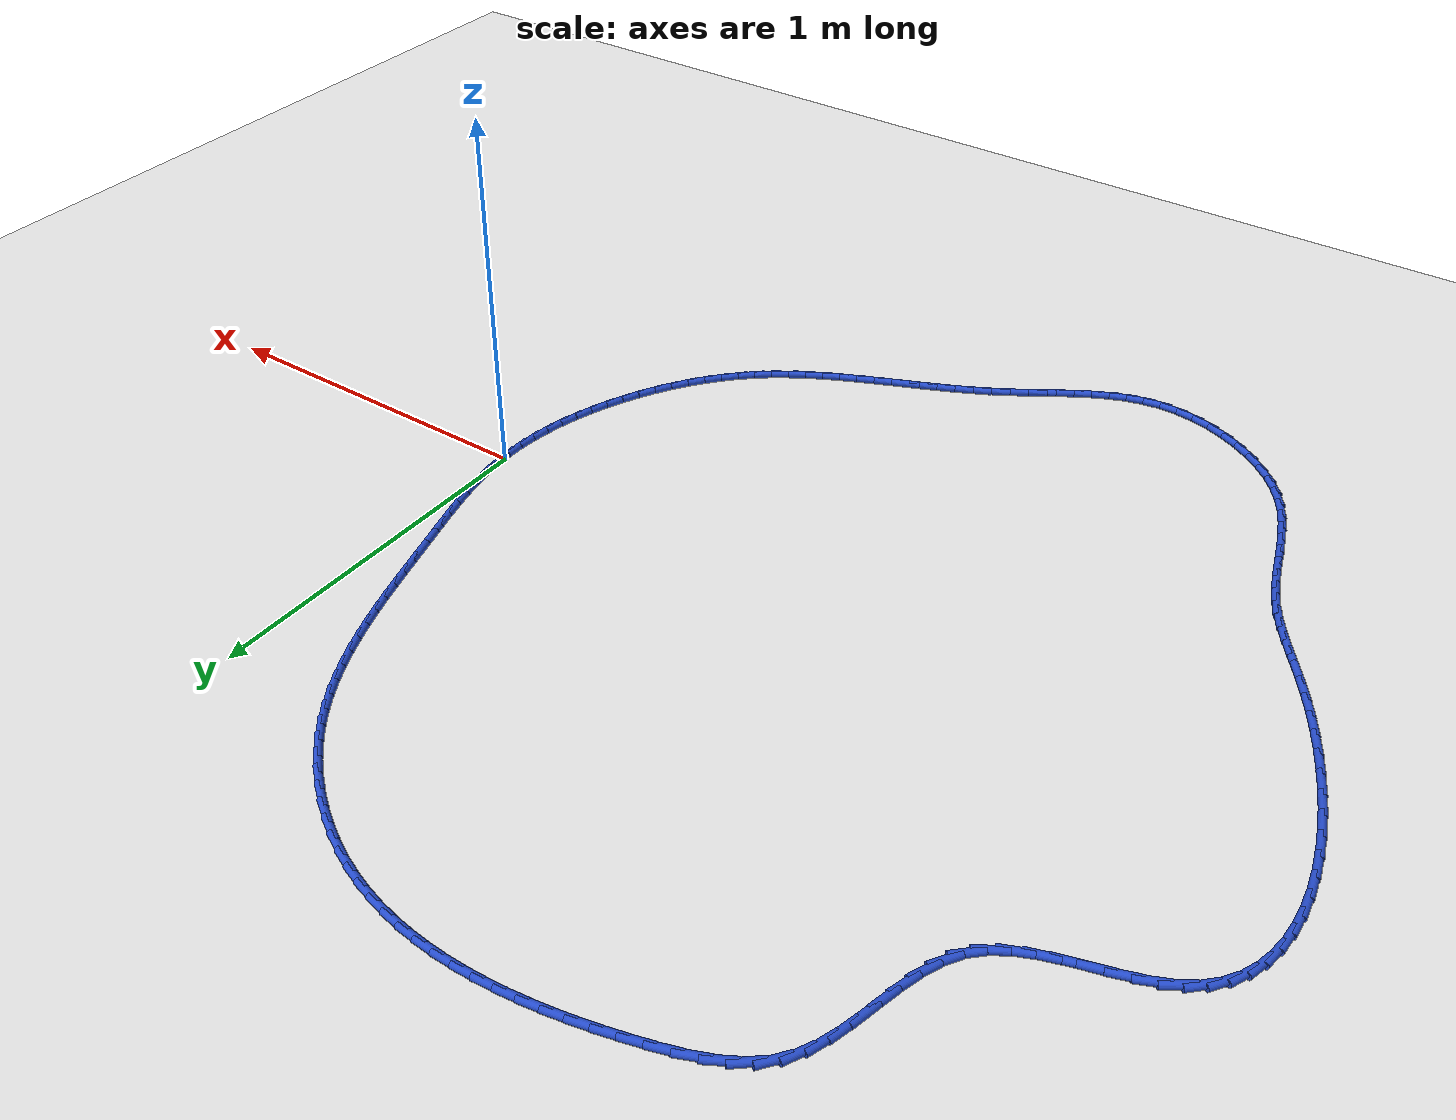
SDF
<sdf version="1.6">
 <world name="default">
  <light name="sun" type="directional">
   <pose>0 0 10 0 -0 0</pose>
   <diffuse>0.8 0.8 0.8 1</diffuse>
   <specular>0.2 0.2 0.2 1</specular>
   <attenuation>
    <range>1000</range>
    <constant>0.9</constant>
    <linear>0.01</linear>
    <quadratic>0.001</quadratic>
   </attenuation>
   <direction>-0.5 0.1 -0.9</direction>
  </light>
  <model name="ground_plane">
   <static>1</static>
   <link name="link">
    <collision name="collision">
     <geometry><plane><normal>0 0 1</normal><size>100 100</size></plane></geometry>
     <surface><friction><ode><mu>100</mu><mu2>50</mu2></ode></friction></surface>
    </collision>
    <visual name="visual">
     <cast_shadows>0</cast_shadows>
     <geometry><plane><normal>0 0 1</normal><size>100 100</size></plane></geometry>
     <material>
      <script><uri>file://media/materials/scripts/gazebo.material</uri><name>Gazebo/WhiteGlow</name></script>
     </material>
    </visual>
   </link>
  </model>
  <gravity>0 0 -9.8</gravity>
  <magnetic_field>6e-06 2.3e-05 -4.2e-05</magnetic_field>
  <atmosphere type="adiabatic"/>
  <physics name="default_physics" default="0" type="ode">
   <max_step_size>0.001</max_step_size>
   <real_time_factor>1</real_time_factor>
   <real_time_update_rate>1000</real_time_update_rate>
  </physics>
  <scene><ambient>0.4 0.4 0.4 1</ambient><background>0.7 0.7 0.7 1</background><shadows>1</shadows></scene>
  <spherical_coordinates>
   <surface_model>EARTH_WGS84</surface_model>
   <latitude_deg>0</latitude_deg>
   <longitude_deg>0</longitude_deg>
   <elevation>0</elevation>
   <heading_deg>0</heading_deg>
  </spherical_coordinates>
  <model name="line">
   <link name="link_0">
    <pose>-2.0816681711721685e-17 1.1102230246251565e-16 0.01 0 1.57 -1.505520157094934</pose>
    <collision name="collision">
     <geometry><cylinder><radius>0.01</radius><length>0.08</length></cylinder></geometry>
    </collision>
    <visual name="visual">
     <material>
      <script><name>Gazebo/Blue</name><uri>file://media/materials/scripts/gazebo.material</uri></script>
     </material>
     <geometry><cylinder><radius>0.01</radius><length>0.08</length></cylinder></geometry>
    </visual>
   </link>
   <link name="link_1">
    <pose>-0.003271948268267561 0.050053483975474274 0.01 0 1.57 -1.4469356911556839</pose>
    <collision name="collision">
     <geometry><cylinder><radius>0.01</radius><length>0.08</length></cylinder></geometry>
    </collision>
    <visual name="visual">
     <material>
      <script><name>Gazebo/Blue</name><uri>file://media/materials/scripts/gazebo.material</uri></script>
     </material>
     <geometry><cylinder><radius>0.01</radius><length>0.08</length></cylinder></geometry>
    </visual>
   </link>
   <link name="link_2">
    <pose>-0.009475955514449162 0.0998856889226639 0.01 0 1.57 -1.3974361151422579</pose>
    <collision name="collision">
     <geometry><cylinder><radius>0.01</radius><length>0.08</length></cylinder></geometry>
    </collision>
    <visual name="visual">
     <material>
      <script><name>Gazebo/Blue</name><uri>file://media/materials/scripts/gazebo.material</uri></script>
     </material>
     <geometry><cylinder><radius>0.01</radius><length>0.08</length></cylinder></geometry>
    </visual>
   </link>
   <link name="link_3">
    <pose>-0.018173702694715535 0.1495535952658225 0.01 0 1.57 -1.357137830975622</pose>
    <collision name="collision">
     <geometry><cylinder><radius>0.01</radius><length>0.08</length></cylinder></geometry>
    </collision>
    <visual name="visual">
     <material>
      <script><name>Gazebo/Blue</name><uri>file://media/materials/scripts/gazebo.material</uri></script>
     </material>
     <geometry><cylinder><radius>0.01</radius><length>0.08</length></cylinder></geometry>
    </visual>
   </link>
   <link name="link_4">
    <pose>-0.028926870765237395 0.1991141834292035 0.01 0 1.57 -1.3259563004419235</pose>
    <collision name="collision">
     <geometry><cylinder><radius>0.01</radius><length>0.08</length></cylinder></geometry>
    </collision>
    <visual name="visual">
     <material>
      <script><name>Gazebo/Blue</name><uri>file://media/materials/scripts/gazebo.material</uri></script>
     </material>
     <geometry><cylinder><radius>0.01</radius><length>0.08</length></cylinder></geometry>
    </visual>
   </link>
   <link name="link_5">
    <pose>-0.04129714068218546 0.2486244338370604 0.01 0 1.57 -1.3037090255967154</pose>
    <collision name="collision">
     <geometry><cylinder><radius>0.01</radius><length>0.08</length></cylinder></geometry>
    </collision>
    <visual name="visual">
     <material>
      <script><name>Gazebo/Blue</name><uri>file://media/materials/scripts/gazebo.material</uri></script>
     </material>
     <geometry><cylinder><radius>0.01</radius><length>0.08</length></cylinder></geometry>
    </visual>
   </link>
   <link name="link_6">
    <pose>-0.05484619340173044 0.2981413269136467 0.01 0 1.57 -1.290192399395464</pose>
    <collision name="collision">
     <geometry><cylinder><radius>0.01</radius><length>0.08</length></cylinder></geometry>
    </collision>
    <visual name="visual">
     <material>
      <script><name>Gazebo/Blue</name><uri>file://media/materials/scripts/gazebo.material</uri></script>
     </material>
     <geometry><cylinder><radius>0.01</radius><length>0.08</length></cylinder></geometry>
    </visual>
   </link>
   <link name="link_7">
    <pose>-0.06913570988004306 0.34772184308321574 0.01 0 1.57 -1.2852322684059707</pose>
    <collision name="collision">
     <geometry><cylinder><radius>0.01</radius><length>0.08</length></cylinder></geometry>
    </collision>
    <visual name="visual">
     <material>
      <script><name>Gazebo/Blue</name><uri>file://media/materials/scripts/gazebo.material</uri></script>
     </material>
     <geometry><cylinder><radius>0.01</radius><length>0.08</length></cylinder></geometry>
    </visual>
   </link>
   <link name="link_8">
    <pose>-0.08372737107329403 0.3974229627700211 0.01 0 1.57 -1.2875415427569228</pose>
    <collision name="collision">
     <geometry><cylinder><radius>0.01</radius><length>0.08</length></cylinder></geometry>
    </collision>
    <visual name="visual">
     <material>
      <script><name>Gazebo/Blue</name><uri>file://media/materials/scripts/gazebo.material</uri></script>
     </material>
     <geometry><cylinder><radius>0.01</radius><length>0.08</length></cylinder></geometry>
    </visual>
   </link>
   <link name="link_9">
    <pose>-0.09824111633993482 0.4472844022798528 0.01 0 1.57 -1.288787930718818</pose>
    <collision name="collision">
     <geometry><cylinder><radius>0.01</radius><length>0.08</length></cylinder></geometry>
    </collision>
    <visual name="visual">
     <material>
      <script><name>Gazebo/Blue</name><uri>file://media/materials/scripts/gazebo.material</uri></script>
     </material>
     <geometry><cylinder><radius>0.01</radius><length>0.08</length></cylinder></geometry>
    </visual>
   </link>
   <link name="link_10">
    <pose>-0.11270996417035418 0.4972234672997843 0.01 0 1.57 -1.285398678195648</pose>
    <collision name="collision">
     <geometry><cylinder><radius>0.01</radius><length>0.08</length></cylinder></geometry>
    </collision>
    <visual name="visual">
     <material>
      <script><name>Gazebo/Blue</name><uri>file://media/materials/scripts/gazebo.material</uri></script>
     </material>
     <geometry><cylinder><radius>0.01</radius><length>0.08</length></cylinder></geometry>
    </visual>
   </link>
   <link name="link_11">
    <pose>-0.12734544840702056 0.5471045628181891 0.01 0 1.57 -1.2773435138953182</pose>
    <collision name="collision">
     <geometry><cylinder><radius>0.01</radius><length>0.08</length></cylinder></geometry>
    </collision>
    <visual name="visual">
     <material>
      <script><name>Gazebo/Blue</name><uri>file://media/materials/scripts/gazebo.material</uri></script>
     </material>
     <geometry><cylinder><radius>0.01</radius><length>0.08</length></cylinder></geometry>
    </visual>
   </link>
   <link name="link_12">
    <pose>-0.14235981227871014 0.5967918836060497 0.01 0 1.57 -1.2645705554632696</pose>
    <collision name="collision">
     <geometry><cylinder><radius>0.01</radius><length>0.08</length></cylinder></geometry>
    </collision>
    <visual name="visual">
     <material>
      <script><name>Gazebo/Blue</name><uri>file://media/materials/scripts/gazebo.material</uri></script>
     </material>
     <geometry><cylinder><radius>0.01</radius><length>0.08</length></cylinder></geometry>
    </visual>
   </link>
   <link name="link_13">
    <pose>-0.15796529901419906 0.6461496244343495 0.01 0 1.57 -1.2469965312548537</pose>
    <collision name="collision">
     <geometry><cylinder><radius>0.01</radius><length>0.08</length></cylinder></geometry>
    </collision>
    <visual name="visual">
     <material>
      <script><name>Gazebo/Blue</name><uri>file://media/materials/scripts/gazebo.material</uri></script>
     </material>
     <geometry><cylinder><radius>0.01</radius><length>0.08</length></cylinder></geometry>
    </visual>
   </link>
   <link name="link_14">
    <pose>-0.1743741518422635 0.6950419800740714 0.01 0 1.57 -1.2245142107115385</pose>
    <collision name="collision">
     <geometry><cylinder><radius>0.01</radius><length>0.08</length></cylinder></geometry>
    </collision>
    <visual name="visual">
     <material>
      <script><name>Gazebo/Blue</name><uri>file://media/materials/scripts/gazebo.material</uri></script>
     </material>
     <geometry><cylinder><radius>0.01</radius><length>0.08</length></cylinder></geometry>
    </visual>
   </link>
   <link name="link_15">
    <pose>-0.19179861399167972 0.7433331452961986 0.01 0 1.57 -1.1970035176301614</pose>
    <collision name="collision">
     <geometry><cylinder><radius>0.01</radius><length>0.08</length></cylinder></geometry>
    </collision>
    <visual name="visual">
     <material>
      <script><name>Gazebo/Blue</name><uri>file://media/materials/scripts/gazebo.material</uri></script>
     </material>
     <geometry><cylinder><radius>0.01</radius><length>0.08</length></cylinder></geometry>
    </visual>
   </link>
   <link name="link_16">
    <pose>-0.2104509286912239 0.7908873148717145 0.01 0 1.57 -1.1643471920368038</pose>
    <collision name="collision">
     <geometry><cylinder><radius>0.01</radius><length>0.08</length></cylinder></geometry>
    </collision>
    <visual name="visual">
     <material>
      <script><name>Gazebo/Blue</name><uri>file://media/materials/scripts/gazebo.material</uri></script>
     </material>
     <geometry><cylinder><radius>0.01</radius><length>0.08</length></cylinder></geometry>
    </visual>
   </link>
   <link name="link_17">
    <pose>-0.23054333916967226 0.8375686835716019 0.01 0 1.57 -1.1264518139641115</pose>
    <collision name="collision">
     <geometry><cylinder><radius>0.01</radius><length>0.08</length></cylinder></geometry>
    </collision>
    <visual name="visual">
     <material>
      <script><name>Gazebo/Blue</name><uri>file://media/materials/scripts/gazebo.material</uri></script>
     </material>
     <geometry><cylinder><radius>0.01</radius><length>0.08</length></cylinder></geometry>
    </visual>
   </link>
   <link name="link_18">
    <pose>-0.25228808865580094 0.8832414461668436 0.01 0 1.57 -1.0832746101532338</pose>
    <collision name="collision">
     <geometry><cylinder><radius>0.01</radius><length>0.08</length></cylinder></geometry>
    </collision>
    <visual name="visual">
     <material>
      <script><name>Gazebo/Blue</name><uri>file://media/materials/scripts/gazebo.material</uri></script>
     </material>
     <geometry><cylinder><radius>0.01</radius><length>0.08</length></cylinder></geometry>
    </visual>
   </link>
   <link name="link_19">
    <pose>-0.27589742037838605 0.9277697974284231 0.01 0 1.57 -1.0348555623011204</pose>
    <collision name="collision">
     <geometry><cylinder><radius>0.01</radius><length>0.08</length></cylinder></geometry>
    </collision>
    <visual name="visual">
     <material>
      <script><name>Gazebo/Blue</name><uri>file://media/materials/scripts/gazebo.material</uri></script>
     </material>
     <geometry><cylinder><radius>0.01</radius><length>0.08</length></cylinder></geometry>
    </visual>
   </link>
   <link name="link_20">
    <pose>-0.3015835775662039 0.9710179321273233 0.01 0 1.57 -0.9813527958579571</pose>
    <collision name="collision">
     <geometry><cylinder><radius>0.01</radius><length>0.08</length></cylinder></geometry>
    </collision>
    <visual name="visual">
     <material>
      <script><name>Gazebo/Blue</name><uri>file://media/materials/scripts/gazebo.material</uri></script>
     </material>
     <geometry><cylinder><radius>0.01</radius><length>0.08</length></cylinder></geometry>
    </visual>
   </link>
   <link name="link_21">
    <pose>-0.32955880344803073 1.0128500450345275 0.01 0 1.57 -0.9230771065466133</pose>
    <collision name="collision">
     <geometry><cylinder><radius>0.01</radius><length>0.08</length></cylinder></geometry>
    </collision>
    <visual name="visual">
     <material>
      <script><name>Gazebo/Blue</name><uri>file://media/materials/scripts/gazebo.material</uri></script>
     </material>
     <geometry><cylinder><radius>0.01</radius><length>0.08</length></cylinder></geometry>
    </visual>
   </link>
   <link name="link_22">
    <pose>-0.3600353412526427 1.0531303309210187 0.01 0 1.57 -0.8611142817440818</pose>
    <collision name="collision">
     <geometry><cylinder><radius>0.01</radius><length>0.08</length></cylinder></geometry>
    </collision>
    <visual name="visual">
     <material>
      <script><name>Gazebo/Blue</name><uri>file://media/materials/scripts/gazebo.material</uri></script>
     </material>
     <geometry><cylinder><radius>0.01</radius><length>0.08</length></cylinder></geometry>
    </visual>
   </link>
   <link name="link_23">
    <pose>-0.39318225416189273 1.0917192024047568 0.01 0 1.57 -0.799620497931112</pose>
    <collision name="collision">
     <geometry><cylinder><radius>0.01</radius><length>0.08</length></cylinder></geometry>
    </collision>
    <visual name="visual">
     <material>
      <script><name>Gazebo/Blue</name><uri>file://media/materials/scripts/gazebo.material</uri></script>
     </material>
     <geometry><cylinder><radius>0.01</radius><length>0.08</length></cylinder></geometry>
    </visual>
   </link>
   <link name="link_24">
    <pose>-0.42888500808327906 1.1284522317349424 0.01 0 1.57 -0.7396883813663929</pose>
    <collision name="collision">
     <geometry><cylinder><radius>0.01</radius><length>0.08</length></cylinder></geometry>
    </collision>
    <visual name="visual">
     <material>
      <script><name>Gazebo/Blue</name><uri>file://media/materials/scripts/gazebo.material</uri></script>
     </material>
     <geometry><cylinder><radius>0.01</radius><length>0.08</length></cylinder></geometry>
    </visual>
   </link>
   <link name="link_25">
    <pose>-0.46691464316998177 1.163154968575266 0.01 0 1.57 -0.6807321209874171</pose>
    <collision name="collision">
     <geometry><cylinder><radius>0.01</radius><length>0.08</length></cylinder></geometry>
    </collision>
    <visual name="visual">
     <material>
      <script><name>Gazebo/Blue</name><uri>file://media/materials/scripts/gazebo.material</uri></script>
     </material>
     <geometry><cylinder><radius>0.01</radius><length>0.08</length></cylinder></geometry>
    </visual>
   </link>
   <link name="link_26">
    <pose>-0.5070418820450693 1.1956529347768614 0.01 0 1.57 -0.6221686634510214</pose>
    <collision name="collision">
     <geometry><cylinder><radius>0.01</radius><length>0.08</length></cylinder></geometry>
    </collision>
    <visual name="visual">
     <material>
      <script><name>Gazebo/Blue</name><uri>file://media/materials/scripts/gazebo.material</uri></script>
     </material>
     <geometry><cylinder><radius>0.01</radius><length>0.08</length></cylinder></geometry>
    </visual>
   </link>
   <link name="link_27">
    <pose>-0.5490374473316119 1.225771652190864 0.01 0 1.57 -0.5634192476552503</pose>
    <collision name="collision">
     <geometry><cylinder><radius>0.01</radius><length>0.08</length></cylinder></geometry>
    </collision>
    <visual name="visual">
     <material>
      <script><name>Gazebo/Blue</name><uri>file://media/materials/scripts/gazebo.material</uri></script>
     </material>
     <geometry><cylinder><radius>0.01</radius><length>0.08</length></cylinder></geometry>
    </visual>
   </link>
   <link name="link_28">
    <pose>-0.5926720616526775 1.2533366426684072 0.01 0 1.57 -0.5039057011146612</pose>
    <collision name="collision">
     <geometry><cylinder><radius>0.01</radius><length>0.08</length></cylinder></geometry>
    </collision>
    <visual name="visual">
     <material>
      <script><name>Gazebo/Blue</name><uri>file://media/materials/scripts/gazebo.material</uri></script>
     </material>
     <geometry><cylinder><radius>0.01</radius><length>0.08</length></cylinder></geometry>
    </visual>
   </link>
   <link name="link_29">
    <pose>-0.6377164476313361 1.2781734280606258 0.01 0 1.57 -0.44304730307370715</pose>
    <collision name="collision">
     <geometry><cylinder><radius>0.01</radius><length>0.08</length></cylinder></geometry>
    </collision>
    <visual name="visual">
     <material>
      <script><name>Gazebo/Blue</name><uri>file://media/materials/scripts/gazebo.material</uri></script>
     </material>
     <geometry><cylinder><radius>0.01</radius><length>0.08</length></cylinder></geometry>
    </visual>
   </link>
   <link name="link_30">
    <pose>-0.6839413278906561 1.300107530218654 0.01 0 1.57 -0.38026335017406027</pose>
    <collision name="collision">
     <geometry><cylinder><radius>0.01</radius><length>0.08</length></cylinder></geometry>
    </collision>
    <visual name="visual">
     <material>
      <script><name>Gazebo/Blue</name><uri>file://media/materials/scripts/gazebo.material</uri></script>
     </material>
     <geometry><cylinder><radius>0.01</radius><length>0.08</length></cylinder></geometry>
    </visual>
   </link>
   <link name="link_31">
    <pose>-0.7311175666902411 1.31896472751858 0.01 0 1.57 -0.3162058836869966</pose>
    <collision name="collision">
     <geometry><cylinder><radius>0.01</radius><length>0.08</length></cylinder></geometry>
    </collision>
    <visual name="visual">
     <material>
      <script><name>Gazebo/Blue</name><uri>file://media/materials/scripts/gazebo.material</uri></script>
     </material>
     <geometry><cylinder><radius>0.01</radius><length>0.08</length></cylinder></geometry>
    </visual>
   </link>
   <link name="link_32">
    <pose>-0.7790601898240487 1.3346507814823638 0.01 0 1.57 -0.2537855068221282</pose>
    <collision name="collision">
     <geometry><cylinder><radius>0.01</radius><length>0.08</length></cylinder></geometry>
    </collision>
    <visual name="visual">
     <material>
      <script><name>Gazebo/Blue</name><uri>file://media/materials/scripts/gazebo.material</uri></script>
     </material>
     <geometry><cylinder><radius>0.01</radius><length>0.08</length></cylinder></geometry>
    </visual>
   </link>
   <link name="link_33">
    <pose>-0.8276908124971861 1.3472645030027541 0.01 0 1.57 -0.19383127458707317</pose>
    <collision name="collision">
     <geometry><cylinder><radius>0.01</radius><length>0.08</length></cylinder></geometry>
    </collision>
    <visual name="visual">
     <material>
      <script><name>Gazebo/Blue</name><uri>file://media/materials/scripts/gazebo.material</uri></script>
     </material>
     <geometry><cylinder><radius>0.01</radius><length>0.08</length></cylinder></geometry>
    </visual>
   </link>
   <link name="link_34">
    <pose>-0.8769468100171041 1.356933246875766 0.01 0 1.57 -0.1366637141161315</pose>
    <collision name="collision">
     <geometry><cylinder><radius>0.01</radius><length>0.08</length></cylinder></geometry>
    </collision>
    <visual name="visual">
     <material>
      <script><name>Gazebo/Blue</name><uri>file://media/materials/scripts/gazebo.material</uri></script>
     </material>
     <geometry><cylinder><radius>0.01</radius><length>0.08</length></cylinder></geometry>
    </visual>
   </link>
   <link name="link_35">
    <pose>-0.9267655576912519 1.3637843678974135 0.01 0 1.57 -0.08250201217486275</pose>
    <collision name="collision">
     <geometry><cylinder><radius>0.01</radius><length>0.08</length></cylinder></geometry>
    </collision>
    <visual name="visual">
     <material>
      <script><name>Gazebo/Blue</name><uri>file://media/materials/scripts/gazebo.material</uri></script>
     </material>
     <geometry><cylinder><radius>0.01</radius><length>0.08</length></cylinder></geometry>
    </visual>
   </link>
   <link name="link_36">
    <pose>-0.9770844308270807 1.3679452208637113 0.01 0 1.57 -0.031472147533216595</pose>
    <collision name="collision">
     <geometry><cylinder><radius>0.01</radius><length>0.08</length></cylinder></geometry>
    </collision>
    <visual name="visual">
     <material>
      <script><name>Gazebo/Blue</name><uri>file://media/materials/scripts/gazebo.material</uri></script>
     </material>
     <geometry><cylinder><radius>0.01</radius><length>0.08</length></cylinder></geometry>
    </visual>
   </link>
   <link name="link_37">
    <pose>-1.0278408047320402 1.369543160570674 0.01 0 1.57 0.016380273131531314</pose>
    <collision name="collision">
     <geometry><cylinder><radius>0.01</radius><length>0.08</length></cylinder></geometry>
    </collision>
    <visual name="visual">
     <material>
      <script><name>Gazebo/Blue</name><uri>file://media/materials/scripts/gazebo.material</uri></script>
     </material>
     <geometry><cylinder><radius>0.01</radius><length>0.08</length></cylinder></geometry>
    </visual>
   </link>
   <link name="link_38">
    <pose>-1.078972054713581 1.3687055418143155 0.01 0 1.57 0.06107496384941317</pose>
    <collision name="collision">
     <geometry><cylinder><radius>0.01</radius><length>0.08</length></cylinder></geometry>
    </collision>
    <visual name="visual">
     <material>
      <script><name>Gazebo/Blue</name><uri>file://media/materials/scripts/gazebo.material</uri></script>
     </material>
     <geometry><cylinder><radius>0.01</radius><length>0.08</length></cylinder></geometry>
    </visual>
   </link>
   <link name="link_39">
    <pose>-1.1304155560791531 1.3655597193906508 0.01 0 1.57 0.10268168489215396</pose>
    <collision name="collision">
     <geometry><cylinder><radius>0.01</radius><length>0.08</length></cylinder></geometry>
    </collision>
    <visual name="visual">
     <material>
      <script><name>Gazebo/Blue</name><uri>file://media/materials/scripts/gazebo.material</uri></script>
     </material>
     <geometry><cylinder><radius>0.01</radius><length>0.08</length></cylinder></geometry>
    </visual>
   </link>
   <link name="link_40">
    <pose>-1.1821086841362072 1.3602330480956946 0.01 0 1.57 0.14130610139226907</pose>
    <collision name="collision">
     <geometry><cylinder><radius>0.01</radius><length>0.08</length></cylinder></geometry>
    </collision>
    <visual name="visual">
     <material>
      <script><name>Gazebo/Blue</name><uri>file://media/materials/scripts/gazebo.material</uri></script>
     </material>
     <geometry><cylinder><radius>0.01</radius><length>0.08</length></cylinder></geometry>
    </visual>
   </link>
   <link name="link_41">
    <pose>-1.2339888141921938 1.352852882725461 0.01 0 1.57 0.17707753174256854</pose>
    <collision name="collision">
     <geometry><cylinder><radius>0.01</radius><length>0.08</length></cylinder></geometry>
    </collision>
    <visual name="visual">
     <material>
      <script><name>Gazebo/Blue</name><uri>file://media/materials/scripts/gazebo.material</uri></script>
     </material>
     <geometry><cylinder><radius>0.01</radius><length>0.08</length></cylinder></geometry>
    </visual>
   </link>
   <link name="link_42">
    <pose>-1.2859933215545618 1.3435465780759641 0.01 0 1.57 0.2101388712756328</pose>
    <collision name="collision">
     <geometry><cylinder><radius>0.01</radius><length>0.08</length></cylinder></geometry>
    </collision>
    <visual name="visual">
     <material>
      <script><name>Gazebo/Blue</name><uri>file://media/materials/scripts/gazebo.material</uri></script>
     </material>
     <geometry><cylinder><radius>0.01</radius><length>0.08</length></cylinder></geometry>
    </visual>
   </link>
   <link name="link_43">
    <pose>-1.3380595815307628 1.3324414889432195 0.01 0 1.57 0.24063865693385778</pose>
    <collision name="collision">
     <geometry><cylinder><radius>0.01</radius><length>0.08</length></cylinder></geometry>
    </collision>
    <visual name="visual">
     <material>
      <script><name>Gazebo/Blue</name><uri>file://media/materials/scripts/gazebo.material</uri></script>
     </material>
     <geometry><cylinder><radius>0.01</radius><length>0.08</length></cylinder></geometry>
    </visual>
   </link>
   <link name="link_44">
    <pose>-1.3901249694282467 1.319664970123241 0.01 0 1.57 0.2687250530779947</pose>
    <collision name="collision">
     <geometry><cylinder><radius>0.01</radius><length>0.08</length></cylinder></geometry>
    </collision>
    <visual name="visual">
     <material>
      <script><name>Gazebo/Blue</name><uri>file://media/materials/scripts/gazebo.material</uri></script>
     </material>
     <geometry><cylinder><radius>0.01</radius><length>0.08</length></cylinder></geometry>
    </visual>
   </link>
   <link name="link_45">
    <pose>-1.4421268605544642 1.3053443764120432 0.01 0 1.57 0.29578208281840696</pose>
    <collision name="collision">
     <geometry><cylinder><radius>0.01</radius><length>0.08</length></cylinder></geometry>
    </collision>
    <visual name="visual">
     <material>
      <script><name>Gazebo/Blue</name><uri>file://media/materials/scripts/gazebo.material</uri></script>
     </material>
     <geometry><cylinder><radius>0.01</radius><length>0.08</length></cylinder></geometry>
    </visual>
   </link>
   <link name="link_46">
    <pose>-1.4939412234388116 1.2895554664853341 0.01 0 1.57 0.3400278877698269</pose>
    <collision name="collision">
     <geometry><cylinder><radius>0.01</radius><length>0.08</length></cylinder></geometry>
    </collision>
    <visual name="visual">
     <material>
      <script><name>Gazebo/Blue</name><uri>file://media/materials/scripts/gazebo.material</uri></script>
     </material>
     <geometry><cylinder><radius>0.01</radius><length>0.08</length></cylinder></geometry>
    </visual>
   </link>
   <link name="link_47">
    <pose>-1.5445741885886282 1.2716431307229106 0.01 0 1.57 0.41793172445537247</pose>
    <collision name="collision">
     <geometry><cylinder><radius>0.01</radius><length>0.08</length></cylinder></geometry>
    </collision>
    <visual name="visual">
     <material>
      <script><name>Gazebo/Blue</name><uri>file://media/materials/scripts/gazebo.material</uri></script>
     </material>
     <geometry><cylinder><radius>0.01</radius><length>0.08</length></cylinder></geometry>
    </visual>
   </link>
   <link name="link_48">
    <pose>-1.592386486577866 1.250409971932017 0.01 0 1.57 0.5363706370894749</pose>
    <collision name="collision">
     <geometry><cylinder><radius>0.01</radius><length>0.08</length></cylinder></geometry>
    </collision>
    <visual name="visual">
     <material>
      <script><name>Gazebo/Blue</name><uri>file://media/materials/scripts/gazebo.material</uri></script>
     </material>
     <geometry><cylinder><radius>0.01</radius><length>0.08</length></cylinder></geometry>
    </visual>
   </link>
   <link name="link_49">
    <pose>-1.6357235858150836 1.2246457691153152 0.01 0 1.57 0.7026062503880768</pose>
    <collision name="collision">
     <geometry><cylinder><radius>0.01</radius><length>0.08</length></cylinder></geometry>
    </collision>
    <visual name="visual">
     <material>
      <script><name>Gazebo/Blue</name><uri>file://media/materials/scripts/gazebo.material</uri></script>
     </material>
     <geometry><cylinder><radius>0.01</radius><length>0.08</length></cylinder></geometry>
    </visual>
   </link>
   <link name="link_50">
    <pose>-1.6729309547088382 1.1931403012754653 0.01 0 1.57 0.9124516486104004</pose>
    <collision name="collision">
     <geometry><cylinder><radius>0.01</radius><length>0.08</length></cylinder></geometry>
    </collision>
    <visual name="visual">
     <material>
      <script><name>Gazebo/Blue</name><uri>file://media/materials/scripts/gazebo.material</uri></script>
     </material>
     <geometry><cylinder><radius>0.01</radius><length>0.08</length></cylinder></geometry>
    </visual>
   </link>
   <link name="link_51">
    <pose>-1.7025507053916702 1.1548449703549264 0.01 0 1.57 1.0993478593963975</pose>
    <collision name="collision">
     <geometry><cylinder><radius>0.01</radius><length>0.08</length></cylinder></geometry>
    </collision>
    <visual name="visual">
     <material>
      <script><name>Gazebo/Blue</name><uri>file://media/materials/scripts/gazebo.material</uri></script>
     </material>
     <geometry><cylinder><radius>0.01</radius><length>0.08</length></cylinder></geometry>
    </visual>
   </link>
   <link name="link_52">
    <pose>-1.7251998454278765 1.110416550289016 0.01 0 1.57 1.2262747372114815</pose>
    <collision name="collision">
     <geometry><cylinder><radius>0.01</radius><length>0.08</length></cylinder></geometry>
    </collision>
    <visual name="visual">
     <material>
      <script><name>Gazebo/Blue</name><uri>file://media/materials/scripts/gazebo.material</uri></script>
     </material>
     <geometry><cylinder><radius>0.01</radius><length>0.08</length></cylinder></geometry>
    </visual>
   </link>
   <link name="link_53">
    <pose>-1.7427401635996478 1.0615349099573759 0.01 0 1.57 1.3004707611511221</pose>
    <collision name="collision">
     <geometry><cylinder><radius>0.01</radius><length>0.08</length></cylinder></geometry>
    </collision>
    <visual name="visual">
     <material>
      <script><name>Gazebo/Blue</name><uri>file://media/materials/scripts/gazebo.material</uri></script>
     </material>
     <geometry><cylinder><radius>0.01</radius><length>0.08</length></cylinder></geometry>
    </visual>
   </link>
   <link name="link_54">
    <pose>-1.7570503583417934 1.009893816408945 0.01 0 1.57 1.3297128883565341</pose>
    <collision name="collision">
     <geometry><cylinder><radius>0.01</radius><length>0.08</length></cylinder></geometry>
    </collision>
    <visual name="visual">
     <material>
      <script><name>Gazebo/Blue</name><uri>file://media/materials/scripts/gazebo.material</uri></script>
     </material>
     <geometry><cylinder><radius>0.01</radius><length>0.08</length></cylinder></geometry>
    </visual>
   </link>
   <link name="link_55">
    <pose>-1.7700091280891206 0.9571870366926637 0.01 0 1.57 1.317407280994206</pose>
    <collision name="collision">
     <geometry><cylinder><radius>0.01</radius><length>0.08</length></cylinder></geometry>
    </collision>
    <visual name="visual">
     <material>
      <script><name>Gazebo/Blue</name><uri>file://media/materials/scripts/gazebo.material</uri></script>
     </material>
     <geometry><cylinder><radius>0.01</radius><length>0.08</length></cylinder></geometry>
    </visual>
   </link>
   <link name="link_56">
    <pose>-1.7834951712764393 0.9051083378574708 0.01 0 1.57 1.261643636834052</pose>
    <collision name="collision">
     <geometry><cylinder><radius>0.01</radius><length>0.08</length></cylinder></geometry>
    </collision>
    <visual name="visual">
     <material>
      <script><name>Gazebo/Blue</name><uri>file://media/materials/scripts/gazebo.material</uri></script>
     </material>
     <geometry><cylinder><radius>0.01</radius><length>0.08</length></cylinder></geometry>
    </visual>
   </link>
   <link name="link_57">
    <pose>-1.7993871863385578 0.8553514869523053 0.01 0 1.57 1.1553641044262903</pose>
    <collision name="collision">
     <geometry><cylinder><radius>0.01</radius><length>0.08</length></cylinder></geometry>
    </collision>
    <visual name="visual">
     <material>
      <script><name>Gazebo/Blue</name><uri>file://media/materials/scripts/gazebo.material</uri></script>
     </material>
     <geometry><cylinder><radius>0.01</radius><length>0.08</length></cylinder></geometry>
    </visual>
   </link>
   <link name="link_58">
    <pose>-1.8195638717102856 0.8096102510261067 0.01 0 1.57 0.9888335363719037</pose>
    <collision name="collision">
     <geometry><cylinder><radius>0.01</radius><length>0.08</length></cylinder></geometry>
    </collision>
    <visual name="visual">
     <material>
      <script><name>Gazebo/Blue</name><uri>file://media/materials/scripts/gazebo.material</uri></script>
     </material>
     <geometry><cylinder><radius>0.01</radius><length>0.08</length></cylinder></geometry>
    </visual>
   </link>
   <link name="link_59">
    <pose>-1.8459039258264307 0.769578397127815 0.01 0 1.57 0.7646317456555336</pose>
    <collision name="collision">
     <geometry><cylinder><radius>0.01</radius><length>0.08</length></cylinder></geometry>
    </collision>
    <visual name="visual">
     <material>
      <script><name>Gazebo/Blue</name><uri>file://media/materials/scripts/gazebo.material</uri></script>
     </material>
     <geometry><cylinder><radius>0.01</radius><length>0.08</length></cylinder></geometry>
    </visual>
   </link>
   <link name="link_60">
    <pose>-1.8800940084416848 0.7367796328952851 0.01 0 1.57 0.5595015557187593</pose>
    <collision name="collision">
     <geometry><cylinder><radius>0.01</radius><length>0.08</length></cylinder></geometry>
    </collision>
    <visual name="visual">
     <material>
      <script><name>Gazebo/Blue</name><uri>file://media/materials/scripts/gazebo.material</uri></script>
     </material>
     <geometry><cylinder><radius>0.01</radius><length>0.08</length></cylinder></geometry>
    </visual>
   </link>
   <link name="link_61">
    <pose>-1.9216100688767817 0.7107799764308866 0.01 0 1.57 0.41899233665328234</pose>
    <collision name="collision">
     <geometry><cylinder><radius>0.01</radius><length>0.08</length></cylinder></geometry>
    </collision>
    <visual name="visual">
     <material>
      <script><name>Gazebo/Blue</name><uri>file://media/materials/scripts/gazebo.material</uri></script>
     </material>
     <geometry><cylinder><radius>0.01</radius><length>0.08</length></cylinder></geometry>
    </visual>
   </link>
   <link name="link_62">
    <pose>-1.9685120468771962 0.6898915018174295 0.01 0 1.57 0.33440838203354933</pose>
    <collision name="collision">
     <geometry><cylinder><radius>0.01</radius><length>0.08</length></cylinder></geometry>
    </collision>
    <visual name="visual">
     <material>
      <script><name>Gazebo/Blue</name><uri>file://media/materials/scripts/gazebo.material</uri></script>
     </material>
     <geometry><cylinder><radius>0.01</radius><length>0.08</length></cylinder></geometry>
    </visual>
   </link>
   <link name="link_63">
    <pose>-2.018836738522389 0.6724057883175673 0.01 0 1.57 0.2959879984718707</pose>
    <collision name="collision">
     <geometry><cylinder><radius>0.01</radius><length>0.08</length></cylinder></geometry>
    </collision>
    <visual name="visual">
     <material>
      <script><name>Gazebo/Blue</name><uri>file://media/materials/scripts/gazebo.material</uri></script>
     </material>
     <geometry><cylinder><radius>0.01</radius><length>0.08</length></cylinder></geometry>
    </visual>
   </link>
   <link name="link_64">
    <pose>-2.0706209398918247 0.6566144151939529 0.01 0 1.57 0.29897691717742214</pose>
    <collision name="collision">
     <geometry><cylinder><radius>0.01</radius><length>0.08</length></cylinder></geometry>
    </collision>
    <visual name="visual">
     <material>
      <script><name>Gazebo/Blue</name><uri>file://media/materials/scripts/gazebo.material</uri></script>
     </material>
     <geometry><cylinder><radius>0.01</radius><length>0.08</length></cylinder></geometry>
    </visual>
   </link>
   <link name="link_65">
    <pose>-2.121901447064964 0.6408089617092402 0.01 0 1.57 0.34474023818986305</pose>
    <collision name="collision">
     <geometry><cylinder><radius>0.01</radius><length>0.08</length></cylinder></geometry>
    </collision>
    <visual name="visual">
     <material>
      <script><name>Gazebo/Blue</name><uri>file://media/materials/scripts/gazebo.material</uri></script>
     </material>
     <geometry><cylinder><radius>0.01</radius><length>0.08</length></cylinder></geometry>
    </visual>
   </link>
   <link name="link_66">
    <pose>-2.170715056121269 0.6232810071260817 0.01 0 1.57 0.44117944549381877</pose>
    <collision name="collision">
     <geometry><cylinder><radius>0.01</radius><length>0.08</length></cylinder></geometry>
    </collision>
    <visual name="visual">
     <material>
      <script><name>Gazebo/Blue</name><uri>file://media/materials/scripts/gazebo.material</uri></script>
     </material>
     <geometry><cylinder><radius>0.01</radius><length>0.08</length></cylinder></geometry>
    </visual>
   </link>
   <link name="link_67">
    <pose>-2.215098563140205 0.6023221307071311 0.01 0 1.57 0.5991140425973632</pose>
    <collision name="collision">
     <geometry><cylinder><radius>0.01</radius><length>0.08</length></cylinder></geometry>
    </collision>
    <visual name="visual">
     <material>
      <script><name>Gazebo/Blue</name><uri>file://media/materials/scripts/gazebo.material</uri></script>
     </material>
     <geometry><cylinder><radius>0.01</radius><length>0.08</length></cylinder></geometry>
    </visual>
   </link>
   <link name="link_68">
    <pose>-2.2531852712303357 0.5763151182761957 0.01 0 1.57 0.7891544901374089</pose>
    <collision name="collision">
     <geometry><cylinder><radius>0.01</radius><length>0.08</length></cylinder></geometry>
    </collision>
    <visual name="visual">
     <material>
      <script><name>Gazebo/Blue</name><uri>file://media/materials/scripts/gazebo.material</uri></script>
     </material>
     <geometry><cylinder><radius>0.01</radius><length>0.08</length></cylinder></geometry>
    </visual>
   </link>
   <link name="link_69">
    <pose>-2.2844008505114166 0.5448641418289798 0.01 0 1.57 0.9749748053602884</pose>
    <collision name="collision">
     <geometry><cylinder><radius>0.01</radius><length>0.08</length></cylinder></geometry>
    </collision>
    <visual name="visual">
     <material>
      <script><name>Gazebo/Blue</name><uri>file://media/materials/scripts/gazebo.material</uri></script>
     </material>
     <geometry><cylinder><radius>0.01</radius><length>0.08</length></cylinder></geometry>
    </visual>
   </link>
   <link name="link_70">
    <pose>-2.309093561520341 0.5084452922263919 0.01 0 1.57 1.1451659990528074</pose>
    <collision name="collision">
     <geometry><cylinder><radius>0.01</radius><length>0.08</length></cylinder></geometry>
    </collision>
    <visual name="visual">
     <material>
      <script><name>Gazebo/Blue</name><uri>file://media/materials/scripts/gazebo.material</uri></script>
     </material>
     <geometry><cylinder><radius>0.01</radius><length>0.08</length></cylinder></geometry>
    </visual>
   </link>
   <link name="link_71">
    <pose>-2.3276315727988393 0.4675534749242701 0.01 0 1.57 1.2939083558724913</pose>
    <collision name="collision">
     <geometry><cylinder><radius>0.01</radius><length>0.08</length></cylinder></geometry>
    </collision>
    <visual name="visual">
     <material>
      <script><name>Gazebo/Blue</name><uri>file://media/materials/scripts/gazebo.material</uri></script>
     </material>
     <geometry><cylinder><radius>0.01</radius><length>0.08</length></cylinder></geometry>
    </visual>
   </link>
   <link name="link_72">
    <pose>-2.3403830528886425 0.42268359537845446 0.01 0 1.57 1.4202854074309041</pose>
    <collision name="collision">
     <geometry><cylinder><radius>0.01</radius><length>0.08</length></cylinder></geometry>
    </collision>
    <visual name="visual">
     <material>
      <script><name>Gazebo/Blue</name><uri>file://media/materials/scripts/gazebo.material</uri></script>
     </material>
     <geometry><cylinder><radius>0.01</radius><length>0.08</length></cylinder></geometry>
    </visual>
   </link>
   <link name="link_73">
    <pose>-2.347716170331481 0.3743305590447833 0.01 0 1.57 1.5263599554041218</pose>
    <collision name="collision">
     <geometry><cylinder><radius>0.01</radius><length>0.08</length></cylinder></geometry>
    </collision>
    <visual name="visual">
     <material>
      <script><name>Gazebo/Blue</name><uri>file://media/materials/scripts/gazebo.material</uri></script>
     </material>
     <geometry><cylinder><radius>0.01</radius><length>0.08</length></cylinder></geometry>
    </visual>
   </link>
   <link name="link_74">
    <pose>-2.3499990936690844 0.32298927137909567 0.01 0 1.57 -1.526261502807037</pose>
    <collision name="collision">
     <geometry><cylinder><radius>0.01</radius><length>0.08</length></cylinder></geometry>
    </collision>
    <visual name="visual">
     <material>
      <script><name>Gazebo/Blue</name><uri>file://media/materials/scripts/gazebo.material</uri></script>
     </material>
     <geometry><cylinder><radius>0.01</radius><length>0.08</length></cylinder></geometry>
    </visual>
   </link>
   <link name="link_75">
    <pose>-2.3475999914431847 0.26915463783723054 0.01 0 1.57 -1.4511380454373817</pose>
    <collision name="collision">
     <geometry><cylinder><radius>0.01</radius><length>0.08</length></cylinder></geometry>
    </collision>
    <visual name="visual">
     <material>
      <script><name>Gazebo/Blue</name><uri>file://media/materials/scripts/gazebo.material</uri></script>
     </material>
     <geometry><cylinder><radius>0.01</radius><length>0.08</length></cylinder></geometry>
    </visual>
   </link>
   <link name="link_76">
    <pose>-2.340887032195511 0.2133215638750264 0.01 0 1.57 -1.3869983255489953</pose>
    <collision name="collision">
     <geometry><cylinder><radius>0.01</radius><length>0.08</length></cylinder></geometry>
    </collision>
    <visual name="visual">
     <material>
      <script><name>Gazebo/Blue</name><uri>file://media/materials/scripts/gazebo.material</uri></script>
     </material>
     <geometry><cylinder><radius>0.01</radius><length>0.08</length></cylinder></geometry>
    </visual>
   </link>
   <link name="link_77">
    <pose>-2.330228384467795 0.15598495494832257 0.01 0 1.57 -1.3314737864261392</pose>
    <collision name="collision">
     <geometry><cylinder><radius>0.01</radius><length>0.08</length></cylinder></geometry>
    </collision>
    <visual name="visual">
     <material>
      <script><name>Gazebo/Blue</name><uri>file://media/materials/scripts/gazebo.material</uri></script>
     </material>
     <geometry><cylinder><radius>0.01</radius><length>0.08</length></cylinder></geometry>
    </visual>
   </link>
   <link name="link_78">
    <pose>-2.315992216801766 0.09763971651295889 0.01 0 1.57 -1.282649880915142</pose>
    <collision name="collision">
     <geometry><cylinder><radius>0.01</radius><length>0.08</length></cylinder></geometry>
    </collision>
    <visual name="visual">
     <material>
      <script><name>Gazebo/Blue</name><uri>file://media/materials/scripts/gazebo.material</uri></script>
     </material>
     <geometry><cylinder><radius>0.01</radius><length>0.08</length></cylinder></geometry>
    </visual>
   </link>
   <link name="link_79">
    <pose>-2.2985466977391553 0.03878075402477239 0.01 0 1.57 -1.2389794649873294</pose>
    <collision name="collision">
     <geometry><cylinder><radius>0.01</radius><length>0.08</length></cylinder></geometry>
    </collision>
    <visual name="visual">
     <material>
      <script><name>Gazebo/Blue</name><uri>file://media/materials/scripts/gazebo.material</uri></script>
     </material>
     <geometry><cylinder><radius>0.01</radius><length>0.08</length></cylinder></geometry>
    </visual>
   </link>
   <link name="link_80">
    <pose>-2.278259995821694 -0.020097027060395928 0.01 0 1.57 -1.1991921112278094</pose>
    <collision name="collision">
     <geometry><cylinder><radius>0.01</radius><length>0.08</length></cylinder></geometry>
    </collision>
    <visual name="visual">
     <material>
      <script><name>Gazebo/Blue</name><uri>file://media/materials/scripts/gazebo.material</uri></script>
     </material>
     <geometry><cylinder><radius>0.01</radius><length>0.08</length></cylinder></geometry>
    </visual>
   </link>
   <link name="link_81">
    <pose>-2.2555002795911108 -0.07849872128670919 0.01 0 1.57 -1.1622121600459072</pose>
    <collision name="collision">
     <geometry><cylinder><radius>0.01</radius><length>0.08</length></cylinder></geometry>
    </collision>
    <visual name="visual">
     <material>
      <script><name>Gazebo/Blue</name><uri>file://media/materials/scripts/gazebo.material</uri></script>
     </material>
     <geometry><cylinder><radius>0.01</radius><length>0.08</length></cylinder></geometry>
    </visual>
   </link>
   <link name="link_82">
    <pose>-2.230635717589138 -0.13592942319832751 0.01 0 1.57 -1.1270862241740904</pose>
    <collision name="collision">
     <geometry><cylinder><radius>0.01</radius><length>0.08</length></cylinder></geometry>
    </collision>
    <visual name="visual">
     <material>
      <script><name>Gazebo/Blue</name><uri>file://media/materials/scripts/gazebo.material</uri></script>
     </material>
     <geometry><cylinder><radius>0.01</radius><length>0.08</length></cylinder></geometry>
    </visual>
   </link>
   <link name="link_83">
    <pose>-2.2040344783575043 -0.1918942273394108 0.01 0 1.57 -1.0929157698981213</pose>
    <collision name="collision">
     <geometry><cylinder><radius>0.01</radius><length>0.08</length></cylinder></geometry>
    </collision>
    <visual name="visual">
     <material>
      <script><name>Gazebo/Blue</name><uri>file://media/materials/scripts/gazebo.material</uri></script>
     </material>
     <geometry><cylinder><radius>0.01</radius><length>0.08</length></cylinder></geometry>
    </visual>
   </link>
   <link name="link_84">
    <pose>-2.176064730437942 -0.24589822825412228 0.01 0 1.57 -1.0587875387089907</pose>
    <collision name="collision">
     <geometry><cylinder><radius>0.01</radius><length>0.08</length></cylinder></geometry>
    </collision>
    <visual name="visual">
     <material>
      <script><name>Gazebo/Blue</name><uri>file://media/materials/scripts/gazebo.material</uri></script>
     </material>
     <geometry><cylinder><radius>0.01</radius><length>0.08</length></cylinder></geometry>
    </visual>
   </link>
   <link name="link_85">
    <pose>-2.1470946423721804 -0.29744652048662107 0.01 0 1.57 -1.023728122854892</pose>
    <collision name="collision">
     <geometry><cylinder><radius>0.01</radius><length>0.08</length></cylinder></geometry>
    </collision>
    <visual name="visual">
     <material>
      <script><name>Gazebo/Blue</name><uri>file://media/materials/scripts/gazebo.material</uri></script>
     </material>
     <geometry><cylinder><radius>0.01</radius><length>0.08</length></cylinder></geometry>
    </visual>
   </link>
   <link name="link_86">
    <pose>-2.117492867569388 -0.34604743245702063 0.01 0 1.57 -0.9917924505949886</pose>
    <collision name="collision">
     <geometry><cylinder><radius>0.01</radius><length>0.08</length></cylinder></geometry>
    </collision>
    <visual name="visual">
     <material>
      <script><name>Gazebo/Blue</name><uri>file://media/materials/scripts/gazebo.material</uri></script>
     </material>
     <geometry><cylinder><radius>0.01</radius><length>0.08</length></cylinder></geometry>
    </visual>
   </link>
   <link name="link_87">
    <pose>-2.0876915712131496 -0.3916328912522365 0.01 0 1.57 -0.974098748056014</pose>
    <collision name="collision">
     <geometry><cylinder><radius>0.01</radius><length>0.08</length></cylinder></geometry>
    </collision>
    <visual name="visual">
     <material>
      <script><name>Gazebo/Blue</name><uri>file://media/materials/scripts/gazebo.material</uri></script>
     </material>
     <geometry><cylinder><radius>0.01</radius><length>0.08</length></cylinder></geometry>
    </visual>
   </link>
   <link name="link_88">
    <pose>-2.0582489623171987 -0.4349754869527118 0.01 0 1.57 -0.9741045089661325</pose>
    <collision name="collision">
     <geometry><cylinder><radius>0.01</radius><length>0.08</length></cylinder></geometry>
    </collision>
    <visual name="visual">
     <material>
      <script><name>Gazebo/Blue</name><uri>file://media/materials/scripts/gazebo.material</uri></script>
     </material>
     <geometry><cylinder><radius>0.01</radius><length>0.08</length></cylinder></geometry>
    </visual>
   </link>
   <link name="link_89">
    <pose>-2.0297381148047204 -0.4769469527645005 0.01 0 1.57 -0.9935881295561417</pose>
    <collision name="collision">
     <geometry><cylinder><radius>0.01</radius><length>0.08</length></cylinder></geometry>
    </collision>
    <visual name="visual">
     <material>
      <script><name>Gazebo/Blue</name><uri>file://media/materials/scripts/gazebo.material</uri></script>
     </material>
     <geometry><cylinder><radius>0.01</radius><length>0.08</length></cylinder></geometry>
    </visual>
   </link>
   <link name="link_90">
    <pose>-2.0027321025989053 -0.5184190218936544 0.01 0 1.57 -1.0335200632097168</pose>
    <collision name="collision">
     <geometry><cylinder><radius>0.01</radius><length>0.08</length></cylinder></geometry>
    </collision>
    <visual name="visual">
     <material>
      <script><name>Gazebo/Blue</name><uri>file://media/materials/scripts/gazebo.material</uri></script>
     </material>
     <geometry><cylinder><radius>0.01</radius><length>0.08</length></cylinder></geometry>
    </visual>
   </link>
   <link name="link_91">
    <pose>-1.9778039996229417 -0.560263427546225 0.01 0 1.57 -1.0936344714262987</pose>
    <collision name="collision">
     <geometry><cylinder><radius>0.01</radius><length>0.08</length></cylinder></geometry>
    </collision>
    <visual name="visual">
     <material>
      <script><name>Gazebo/Blue</name><uri>file://media/materials/scripts/gazebo.material</uri></script>
     </material>
     <geometry><cylinder><radius>0.01</radius><length>0.08</length></cylinder></geometry>
    </visual>
   </link>
   <link name="link_92">
    <pose>-1.955526879800019 -0.6033519029282669 0.01 0 1.57 -1.1687638068294466</pose>
    <collision name="collision">
     <geometry><cylinder><radius>0.01</radius><length>0.08</length></cylinder></geometry>
    </collision>
    <visual name="visual">
     <material>
      <script><name>Gazebo/Blue</name><uri>file://media/materials/scripts/gazebo.material</uri></script>
     </material>
     <geometry><cylinder><radius>0.01</radius><length>0.08</length></cylinder></geometry>
    </visual>
   </link>
   <link name="link_93">
    <pose>-1.936353764938909 -0.6484448359256604 0.01 0 1.57 -1.2318171107914921</pose>
    <collision name="collision">
     <geometry><cylinder><radius>0.01</radius><length>0.08</length></cylinder></geometry>
    </collision>
    <visual name="visual">
     <material>
      <script><name>Gazebo/Blue</name><uri>file://media/materials/scripts/gazebo.material</uri></script>
     </material>
     <geometry><cylinder><radius>0.01</radius><length>0.08</length></cylinder></geometry>
    </visual>
   </link>
   <link name="link_94">
    <pose>-1.9197896653956894 -0.6954233576178681 0.01 0 1.57 -1.2717337638495754</pose>
    <collision name="collision">
     <geometry><cylinder><radius>0.01</radius><length>0.08</length></cylinder></geometry>
    </collision>
    <visual name="visual">
     <material>
      <script><name>Gazebo/Blue</name><uri>file://media/materials/scripts/gazebo.material</uri></script>
     </material>
     <geometry><cylinder><radius>0.01</radius><length>0.08</length></cylinder></geometry>
    </visual>
   </link>
   <link name="link_95">
    <pose>-1.9048896961175226 -0.7437513323948597 0.01 0 1.57 -1.2897933882129764</pose>
    <collision name="collision">
     <geometry><cylinder><radius>0.01</radius><length>0.08</length></cylinder></geometry>
    </collision>
    <visual name="visual">
     <material>
      <script><name>Gazebo/Blue</name><uri>file://media/materials/scripts/gazebo.material</uri></script>
     </material>
     <geometry><cylinder><radius>0.01</radius><length>0.08</length></cylinder></geometry>
    </visual>
   </link>
   <link name="link_96">
    <pose>-1.8907062557185923 -0.7928901053160055 0.01 0 1.57 -1.286946343406752</pose>
    <collision name="collision">
     <geometry><cylinder><radius>0.01</radius><length>0.08</length></cylinder></geometry>
    </collision>
    <visual name="visual">
     <material>
      <script><name>Gazebo/Blue</name><uri>file://media/materials/scripts/gazebo.material</uri></script>
     </material>
     <geometry><cylinder><radius>0.01</radius><length>0.08</length></cylinder></geometry>
    </visual>
   </link>
   <link name="link_97">
    <pose>-1.8762917428130805 -0.8423010214406778 0.01 0 1.57 -1.2635506510215266</pose>
    <collision name="collision">
     <geometry><cylinder><radius>0.01</radius><length>0.08</length></cylinder></geometry>
    </collision>
    <visual name="visual">
     <material>
      <script><name>Gazebo/Blue</name><uri>file://media/materials/scripts/gazebo.material</uri></script>
     </material>
     <geometry><cylinder><radius>0.01</radius><length>0.08</length></cylinder></geometry>
    </visual>
   </link>
   <link name="link_98">
    <pose>-1.8606985560151708 -0.8914454258282458 0.01 0 1.57 -1.2194413469747363</pose>
    <collision name="collision">
     <geometry><cylinder><radius>0.01</radius><length>0.08</length></cylinder></geometry>
    </collision>
    <visual name="visual">
     <material>
      <script><name>Gazebo/Blue</name><uri>file://media/materials/scripts/gazebo.material</uri></script>
     </material>
     <geometry><cylinder><radius>0.01</radius><length>0.08</length></cylinder></geometry>
    </visual>
   </link>
   <link name="link_99">
    <pose>-1.8429790939390442 -0.9397846635380817 0.01 0 1.57 -1.154234833714511</pose>
    <collision name="collision">
     <geometry><cylinder><radius>0.01</radius><length>0.08</length></cylinder></geometry>
    </collision>
    <visual name="visual">
     <material>
      <script><name>Gazebo/Blue</name><uri>file://media/materials/scripts/gazebo.material</uri></script>
     </material>
     <geometry><cylinder><radius>0.01</radius><length>0.08</length></cylinder></geometry>
    </visual>
   </link>
   <link name="link_100">
    <pose>-1.8221857551988838 -0.9867800796295559 0.01 0 1.57 -1.0679071662905437</pose>
    <collision name="collision">
     <geometry><cylinder><radius>0.01</radius><length>0.08</length></cylinder></geometry>
    </collision>
    <visual name="visual">
     <material>
      <script><name>Gazebo/Blue</name><uri>file://media/materials/scripts/gazebo.material</uri></script>
     </material>
     <geometry><cylinder><radius>0.01</radius><length>0.08</length></cylinder></geometry>
    </visual>
   </link>
   <link name="link_101">
    <pose>-1.7973709384088734 -1.0318930191620386 0.01 0 1.57 -0.9617722979563486</pose>
    <collision name="collision">
     <geometry><cylinder><radius>0.01</radius><length>0.08</length></cylinder></geometry>
    </collision>
    <visual name="visual">
     <material>
      <script><name>Gazebo/Blue</name><uri>file://media/materials/scripts/gazebo.material</uri></script>
     </material>
     <geometry><cylinder><radius>0.01</radius><length>0.08</length></cylinder></geometry>
    </visual>
   </link>
   <link name="link_102">
    <pose>-1.7675946087914445 -1.0745851092813268 0.01 0 1.57 -0.8478183198937854</pose>
    <collision name="collision">
     <geometry><cylinder><radius>0.01</radius><length>0.08</length></cylinder></geometry>
    </collision>
    <visual name="visual">
     <material>
      <script><name>Gazebo/Blue</name><uri>file://media/materials/scripts/gazebo.material</uri></script>
     </material>
     <geometry><cylinder><radius>0.01</radius><length>0.08</length></cylinder></geometry>
    </visual>
   </link>
   <link name="link_103">
    <pose>-1.7325165601273373 -1.1143403390010769 0.01 0 1.57 -0.7413102429178423</pose>
    <collision name="collision">
     <geometry><cylinder><radius>0.01</radius><length>0.08</length></cylinder></geometry>
    </collision>
    <visual name="visual">
     <material>
      <script><name>Gazebo/Blue</name><uri>file://media/materials/scripts/gazebo.material</uri></script>
     </material>
     <geometry><cylinder><radius>0.01</radius><length>0.08</length></cylinder></geometry>
    </visual>
   </link>
   <link name="link_104">
    <pose>-1.6928215665376358 -1.1506809090449612 0.01 0 1.57 -0.6406531763180362</pose>
    <collision name="collision">
     <geometry><cylinder><radius>0.01</radius><length>0.08</length></cylinder></geometry>
    </collision>
    <visual name="visual">
     <material>
      <script><name>Gazebo/Blue</name><uri>file://media/materials/scripts/gazebo.material</uri></script>
     </material>
     <geometry><cylinder><radius>0.01</radius><length>0.08</length></cylinder></geometry>
    </visual>
   </link>
   <link name="link_105">
    <pose>-1.6492947281145003 -1.1831327603322104 0.01 0 1.57 -0.5427043826829959</pose>
    <collision name="collision">
     <geometry><cylinder><radius>0.01</radius><length>0.08</length></cylinder></geometry>
    </collision>
    <visual name="visual">
     <material>
      <script><name>Gazebo/Blue</name><uri>file://media/materials/scripts/gazebo.material</uri></script>
     </material>
     <geometry><cylinder><radius>0.01</radius><length>0.08</length></cylinder></geometry>
    </visual>
   </link>
   <link name="link_106">
    <pose>-1.6027211449500947 -1.2112218337820533 0.01 0 1.57 -0.4443752446883119</pose>
    <collision name="collision">
     <geometry><cylinder><radius>0.01</radius><length>0.08</length></cylinder></geometry>
    </collision>
    <visual name="visual">
     <material>
      <script><name>Gazebo/Blue</name><uri>file://media/materials/scripts/gazebo.material</uri></script>
     </material>
     <geometry><cylinder><radius>0.01</radius><length>0.08</length></cylinder></geometry>
    </visual>
   </link>
   <link name="link_107">
    <pose>-1.5538859171365798 -1.2344740703137207 0.01 0 1.57 -0.3425452752657206</pose>
    <collision name="collision">
     <geometry><cylinder><radius>0.01</radius><length>0.08</length></cylinder></geometry>
    </collision>
    <visual name="visual">
     <material>
      <script><name>Gazebo/Blue</name><uri>file://media/materials/scripts/gazebo.material</uri></script>
     </material>
     <geometry><cylinder><radius>0.01</radius><length>0.08</length></cylinder></geometry>
    </visual>
   </link>
   <link name="link_108">
    <pose>-1.5035741447661182 -1.2524154108464405 0.01 0 1.57 -0.23397997059788855</pose>
    <collision name="collision">
     <geometry><cylinder><radius>0.01</radius><length>0.08</length></cylinder></geometry>
    </collision>
    <visual name="visual">
     <material>
      <script><name>Gazebo/Blue</name><uri>file://media/materials/scripts/gazebo.material</uri></script>
     </material>
     <geometry><cylinder><radius>0.01</radius><length>0.08</length></cylinder></geometry>
    </visual>
   </link>
   <link name="link_109">
    <pose>-1.4525709279308734 -1.2645717962994427 0.01 0 1.57 -0.11532613322053537</pose>
    <collision name="collision">
     <geometry><cylinder><radius>0.01</radius><length>0.08</length></cylinder></geometry>
    </collision>
    <visual name="visual">
     <material>
      <script><name>Gazebo/Blue</name><uri>file://media/materials/scripts/gazebo.material</uri></script>
     </material>
     <geometry><cylinder><radius>0.01</radius><length>0.08</length></cylinder></geometry>
    </visual>
   </link>
   <link name="link_110">
    <pose>-1.4016613667230062 -1.2704691675919577 0.01 0 1.57 0.016702194359765176</pose>
    <collision name="collision">
     <geometry><cylinder><radius>0.01</radius><length>0.08</length></cylinder></geometry>
    </collision>
    <visual name="visual">
     <material>
      <script><name>Gazebo/Blue</name><uri>file://media/materials/scripts/gazebo.material</uri></script>
     </material>
     <geometry><cylinder><radius>0.01</radius><length>0.08</length></cylinder></geometry>
    </visual>
   </link>
   <link name="link_111">
    <pose>-1.3516305612346793 -1.269633465643214 0.01 0 1.57 0.1608272606202004</pose>
    <collision name="collision">
     <geometry><cylinder><radius>0.01</radius><length>0.08</length></cylinder></geometry>
    </collision>
    <visual name="visual">
     <material>
      <script><name>Gazebo/Blue</name><uri>file://media/materials/scripts/gazebo.material</uri></script>
     </material>
     <geometry><cylinder><radius>0.01</radius><length>0.08</length></cylinder></geometry>
    </visual>
   </link>
   <link name="link_112">
    <pose>-1.3031412510930915 -1.2617671234356882 0.01 0 1.57 0.29276295133437574</pose>
    <collision name="collision">
     <geometry><cylinder><radius>0.01</radius><length>0.08</length></cylinder></geometry>
    </collision>
    <visual name="visual">
     <material>
      <script><name>Gazebo/Blue</name><uri>file://media/materials/scripts/gazebo.material</uri></script>
     </material>
     <geometry><cylinder><radius>0.01</radius><length>0.08</length></cylinder></geometry>
    </visual>
   </link>
   <link name="link_113">
    <pose>-1.256143312577792 -1.2476008041328719 0.01 0 1.57 0.3998957443994117</pose>
    <collision name="collision">
     <geometry><cylinder><radius>0.01</radius><length>0.08</length></cylinder></geometry>
    </collision>
    <visual name="visual">
     <material>
      <script><name>Gazebo/Blue</name><uri>file://media/materials/scripts/gazebo.material</uri></script>
     </material>
     <geometry><cylinder><radius>0.01</radius><length>0.08</length></cylinder></geometry>
    </visual>
   </link>
   <link name="link_114">
    <pose>-1.2103291662175528 -1.2282365236604667 0.01 0 1.57 0.48112620298321734</pose>
    <collision name="collision">
     <geometry><cylinder><radius>0.01</radius><length>0.08</length></cylinder></geometry>
    </collision>
    <visual name="visual">
     <material>
      <script><name>Gazebo/Blue</name><uri>file://media/materials/scripts/gazebo.material</uri></script>
     </material>
     <geometry><cylinder><radius>0.01</radius><length>0.08</length></cylinder></geometry>
    </visual>
   </link>
   <link name="link_115">
    <pose>-1.1653908832186506 -1.2047768018050191 0.01 0 1.57 0.5376047639839249</pose>
    <collision name="collision">
     <geometry><cylinder><radius>0.01</radius><length>0.08</length></cylinder></geometry>
    </collision>
    <visual name="visual">
     <material>
      <script><name>Gazebo/Blue</name><uri>file://media/materials/scripts/gazebo.material</uri></script>
     </material>
     <geometry><cylinder><radius>0.01</radius><length>0.08</length></cylinder></geometry>
    </visual>
   </link>
   <link name="link_116">
    <pose>-1.1210205347873652 -1.1783241583530788 0.01 0 1.57 0.5711192318179215</pose>
    <collision name="collision">
     <geometry><cylinder><radius>0.01</radius><length>0.08</length></cylinder></geometry>
    </collision>
    <visual name="visual">
     <material>
      <script><name>Gazebo/Blue</name><uri>file://media/materials/scripts/gazebo.material</uri></script>
     </material>
     <geometry><cylinder><radius>0.01</radius><length>0.08</length></cylinder></geometry>
    </visual>
   </link>
   <link name="link_117">
    <pose>-1.076910192129975 -1.149981113091193 0.01 0 1.57 0.5831595790492958</pose>
    <collision name="collision">
     <geometry><cylinder><radius>0.01</radius><length>0.08</length></cylinder></geometry>
    </collision>
    <visual name="visual">
     <material>
      <script><name>Gazebo/Blue</name><uri>file://media/materials/scripts/gazebo.material</uri></script>
     </material>
     <geometry><cylinder><radius>0.01</radius><length>0.08</length></cylinder></geometry>
    </visual>
   </link>
   <link name="link_118">
    <pose>-1.0327519264527576 -1.12085018580591 0.01 0 1.57 0.5745112430602818</pose>
    <collision name="collision">
     <geometry><cylinder><radius>0.01</radius><length>0.08</length></cylinder></geometry>
    </collision>
    <visual name="visual">
     <material>
      <script><name>Gazebo/Blue</name><uri>file://media/materials/scripts/gazebo.material</uri></script>
     </material>
     <geometry><cylinder><radius>0.01</radius><length>0.08</length></cylinder></geometry>
    </visual>
   </link>
   <link name="link_119">
    <pose>-0.9882378089619919 -1.0920338962837777 0.01 0 1.57 0.5453179801834268</pose>
    <collision name="collision">
     <geometry><cylinder><radius>0.01</radius><length>0.08</length></cylinder></geometry>
    </collision>
    <visual name="visual">
     <material>
      <script><name>Gazebo/Blue</name><uri>file://media/materials/scripts/gazebo.material</uri></script>
     </material>
     <geometry><cylinder><radius>0.01</radius><length>0.08</length></cylinder></geometry>
    </visual>
   </link>
   <link name="link_120">
    <pose>-0.9430626230429862 -1.0646269411257425 0.01 0 1.57 0.5053894721539386</pose>
    <collision name="collision">
     <geometry><cylinder><radius>0.01</radius><length>0.08</length></cylinder></geometry>
    </collision>
    <visual name="visual">
     <material>
      <script><name>Gazebo/Blue</name><uri>file://media/materials/scripts/gazebo.material</uri></script>
     </material>
     <geometry><cylinder><radius>0.01</radius><length>0.08</length></cylinder></geometry>
    </visual>
   </link>
   <link name="link_121">
    <pose>-0.8971038650739853 -1.0391969876920815 0.01 0 1.57 0.47138928524450735</pose>
    <collision name="collision">
     <geometry><cylinder><radius>0.01</radius><length>0.08</length></cylinder></geometry>
    </collision>
    <visual name="visual">
     <material>
      <script><name>Gazebo/Blue</name><uri>file://media/materials/scripts/gazebo.material</uri></script>
     </material>
     <geometry><cylinder><radius>0.01</radius><length>0.08</length></cylinder></geometry>
    </visual>
   </link>
   <link name="link_122">
    <pose>-0.8505343662091261 -1.0154598205065921 0.01 0 1.57 0.44501665496027776</pose>
    <collision name="collision">
     <geometry><cylinder><radius>0.01</radius><length>0.08</length></cylinder></geometry>
    </collision>
    <visual name="visual">
     <material>
      <script><name>Gazebo/Blue</name><uri>file://media/materials/scripts/gazebo.material</uri></script>
     </material>
     <geometry><cylinder><radius>0.01</radius><length>0.08</length></cylinder></geometry>
    </visual>
   </link>
   <link name="link_123">
    <pose>-0.803553835291924 -0.9930536963376666 0.01 0 1.57 0.42638127924646607</pose>
    <collision name="collision">
     <geometry><cylinder><radius>0.01</radius><length>0.08</length></cylinder></geometry>
    </collision>
    <visual name="visual">
     <material>
      <script><name>Gazebo/Blue</name><uri>file://media/materials/scripts/gazebo.material</uri></script>
     </material>
     <geometry><cylinder><radius>0.01</radius><length>0.08</length></cylinder></geometry>
    </visual>
   </link>
   <link name="link_124">
    <pose>-0.7563619811658964 -0.9716168719536996 0.01 0 1.57 0.4155667189112722</pose>
    <collision name="collision">
     <geometry><cylinder><radius>0.01</radius><length>0.08</length></cylinder></geometry>
    </collision>
    <visual name="visual">
     <material>
      <script><name>Gazebo/Blue</name><uri>file://media/materials/scripts/gazebo.material</uri></script>
     </material>
     <geometry><cylinder><radius>0.01</radius><length>0.08</length></cylinder></geometry>
    </visual>
   </link>
   <link name="link_125">
    <pose>-0.7091585126745609 -0.9507876041230848 0.01 0 1.57 0.41266442618233246</pose>
    <collision name="collision">
     <geometry><cylinder><radius>0.01</radius><length>0.08</length></cylinder></geometry>
    </collision>
    <visual name="visual">
     <material>
      <script><name>Gazebo/Blue</name><uri>file://media/materials/scripts/gazebo.material</uri></script>
     </material>
     <geometry><cylinder><radius>0.01</radius><length>0.08</length></cylinder></geometry>
    </visual>
   </link>
   <link name="link_126">
    <pose>-0.6621431386614329 -0.9302041496142149 0.01 0 1.57 0.4177947846652831</pose>
    <collision name="collision">
     <geometry><cylinder><radius>0.01</radius><length>0.08</length></cylinder></geometry>
    </collision>
    <visual name="visual">
     <material>
      <script><name>Gazebo/Blue</name><uri>file://media/materials/scripts/gazebo.material</uri></script>
     </material>
     <geometry><cylinder><radius>0.01</radius><length>0.08</length></cylinder></geometry>
    </visual>
   </link>
   <link name="link_127">
    <pose>-0.6155155679700308 -0.9095047651954841 0.01 0 1.57 0.4311141920474084</pose>
    <collision name="collision">
     <geometry><cylinder><radius>0.01</radius><length>0.08</length></cylinder></geometry>
    </collision>
    <visual name="visual">
     <material>
      <script><name>Gazebo/Blue</name><uri>file://media/materials/scripts/gazebo.material</uri></script>
     </material>
     <geometry><cylinder><radius>0.01</radius><length>0.08</length></cylinder></geometry>
    </visual>
   </link>
   <link name="link_128">
    <pose>-0.56947550944387 -0.8883277076352855 0.01 0 1.57 0.45280670458858957</pose>
    <collision name="collision">
     <geometry><cylinder><radius>0.01</radius><length>0.08</length></cylinder></geometry>
    </collision>
    <visual name="visual">
     <material>
      <script><name>Gazebo/Blue</name><uri>file://media/materials/scripts/gazebo.material</uri></script>
     </material>
     <geometry><cylinder><radius>0.01</radius><length>0.08</length></cylinder></geometry>
    </visual>
   </link>
   <link name="link_129">
    <pose>-0.5242226719264679 -0.8663112337020126 0.01 0 1.57 0.48305787888864155</pose>
    <collision name="collision">
     <geometry><cylinder><radius>0.01</radius><length>0.08</length></cylinder></geometry>
    </collision>
    <visual name="visual">
     <material>
      <script><name>Gazebo/Blue</name><uri>file://media/materials/scripts/gazebo.material</uri></script>
     </material>
     <geometry><cylinder><radius>0.01</radius><length>0.08</length></cylinder></geometry>
    </visual>
   </link>
   <link name="link_130">
    <pose>-0.47995676426134226 -0.8430936001640597 0.01 0 1.57 0.5220079594008806</pose>
    <collision name="collision">
     <geometry><cylinder><radius>0.01</radius><length>0.08</length></cylinder></geometry>
    </collision>
    <visual name="visual">
     <material>
      <script><name>Gazebo/Blue</name><uri>file://media/materials/scripts/gazebo.material</uri></script>
     </material>
     <geometry><cylinder><radius>0.01</radius><length>0.08</length></cylinder></geometry>
    </visual>
   </link>
   <link name="link_131">
    <pose>-0.43687749529200837 -0.8183130637898193 0.01 0 1.57 0.569682554157806</pose>
    <collision name="collision">
     <geometry><cylinder><radius>0.01</radius><length>0.08</length></cylinder></geometry>
    </collision>
    <visual name="visual">
     <material>
      <script><name>Gazebo/Blue</name><uri>file://media/materials/scripts/gazebo.material</uri></script>
     </material>
     <geometry><cylinder><radius>0.01</radius><length>0.08</length></cylinder></geometry>
    </visual>
   </link>
   <link name="link_132">
    <pose>-0.3951845738619844 -0.7916078813476857 0.01 0 1.57 0.625902804945233</pose>
    <collision name="collision">
     <geometry><cylinder><radius>0.01</radius><length>0.08</length></cylinder></geometry>
    </collision>
    <visual name="visual">
     <material>
      <script><name>Gazebo/Blue</name><uri>file://media/materials/scripts/gazebo.material</uri></script>
     </material>
     <geometry><cylinder><radius>0.01</radius><length>0.08</length></cylinder></geometry>
    </visual>
   </link>
   <link name="link_133">
    <pose>-0.3550777088147861 -0.7626163096060521 0.01 0 1.57 0.6900855683961941</pose>
    <collision name="collision">
     <geometry><cylinder><radius>0.01</radius><length>0.08</length></cylinder></geometry>
    </collision>
    <visual name="visual">
     <material>
      <script><name>Gazebo/Blue</name><uri>file://media/materials/scripts/gazebo.material</uri></script>
     </material>
     <geometry><cylinder><radius>0.01</radius><length>0.08</length></cylinder></geometry>
    </visual>
   </link>
   <link name="link_134">
    <pose>-0.31675519068804625 -0.7309818384434488 0.01 0 1.57 0.7570289250053539</pose>
    <collision name="collision">
     <geometry><cylinder><radius>0.01</radius><length>0.08</length></cylinder></geometry>
    </collision>
    <visual name="visual">
     <material>
      <script><name>Gazebo/Blue</name><uri>file://media/materials/scripts/gazebo.material</uri></script>
     </material>
     <geometry><cylinder><radius>0.01</radius><length>0.08</length></cylinder></geometry>
    </visual>
   </link>
   <link name="link_135">
    <pose>-0.2803506833080514 -0.6965864103190059 0.01 0 1.57 0.8204053007574852</pose>
    <collision name="collision">
     <geometry><cylinder><radius>0.01</radius><length>0.08</length></cylinder></geometry>
    </collision>
    <visual name="visual">
     <material>
      <script><name>Gazebo/Blue</name><uri>file://media/materials/scripts/gazebo.material</uri></script>
     </material>
     <geometry><cylinder><radius>0.01</radius><length>0.08</length></cylinder></geometry>
    </visual>
   </link>
   <link name="link_136">
    <pose>-0.24590795392937517 -0.6596436582430965 0.01 0 1.57 0.8800724005517927</pose>
    <collision name="collision">
     <geometry><cylinder><radius>0.01</radius><length>0.08</length></cylinder></geometry>
    </collision>
    <visual name="visual">
     <material>
      <script><name>Gazebo/Blue</name><uri>file://media/materials/scripts/gazebo.material</uri></script>
     </material>
     <geometry><cylinder><radius>0.01</radius><length>0.08</length></cylinder></geometry>
    </visual>
   </link>
   <link name="link_137">
    <pose>-0.2134641243309617 -0.6203917349762186 0.01 0 1.57 0.936407848805233</pose>
    <collision name="collision">
     <geometry><cylinder><radius>0.01</radius><length>0.08</length></cylinder></geometry>
    </collision>
    <visual name="visual">
     <material>
      <script><name>Gazebo/Blue</name><uri>file://media/materials/scripts/gazebo.material</uri></script>
     </material>
     <geometry><cylinder><radius>0.01</radius><length>0.08</length></cylinder></geometry>
    </visual>
   </link>
   <link name="link_138">
    <pose>-0.18305631629175512 -0.5790687932788705 0.01 0 1.57 0.9898186611523031</pose>
    <collision name="collision">
     <geometry><cylinder><radius>0.01</radius><length>0.08</length></cylinder></geometry>
    </collision>
    <visual name="visual">
     <material>
      <script><name>Gazebo/Blue</name><uri>file://media/materials/scripts/gazebo.material</uri></script>
     </material>
     <geometry><cylinder><radius>0.01</radius><length>0.08</length></cylinder></geometry>
    </visual>
   </link>
   <link name="link_139">
    <pose>-0.15472165159069806 -0.5359129859115489 0.01 0 1.57 1.0407246579802425</pose>
    <collision name="collision">
     <geometry><cylinder><radius>0.01</radius><length>0.08</length></cylinder></geometry>
    </collision>
    <visual name="visual">
     <material>
      <script><name>Gazebo/Blue</name><uri>file://media/materials/scripts/gazebo.material</uri></script>
     </material>
     <geometry><cylinder><radius>0.01</radius><length>0.08</length></cylinder></geometry>
    </visual>
   </link>
   <link name="link_140">
    <pose>-0.128497252006735 -0.49116246563475274 0.01 0 1.57 1.089548640955206</pose>
    <collision name="collision">
     <geometry><cylinder><radius>0.01</radius><length>0.08</length></cylinder></geometry>
    </collision>
    <visual name="visual">
     <material>
      <script><name>Gazebo/Blue</name><uri>file://media/materials/scripts/gazebo.material</uri></script>
     </material>
     <geometry><cylinder><radius>0.01</radius><length>0.08</length></cylinder></geometry>
    </visual>
   </link>
   <link name="link_141">
    <pose>-0.10442023931880881 -0.4450553852089787 0.01 0 1.57 1.1367146287888263</pose>
    <collision name="collision">
     <geometry><cylinder><radius>0.01</radius><length>0.08</length></cylinder></geometry>
    </collision>
    <visual name="visual">
     <material>
      <script><name>Gazebo/Blue</name><uri>file://media/materials/scripts/gazebo.material</uri></script>
     </material>
     <geometry><cylinder><radius>0.01</radius><length>0.08</length></cylinder></geometry>
    </visual>
   </link>
   <link name="link_142">
    <pose>-0.08252784875246758 -0.3978297979416385 0.01 0 1.57 1.1833321701903066</pose>
    <collision name="collision">
     <geometry><cylinder><radius>0.01</radius><length>0.08</length></cylinder></geometry>
    </collision>
    <visual name="visual">
     <material>
      <script><name>Gazebo/Blue</name><uri>file://media/materials/scripts/gazebo.material</uri></script>
     </material>
     <geometry><cylinder><radius>0.01</radius><length>0.08</length></cylinder></geometry>
    </visual>
   </link>
   <link name="link_143">
    <pose>-0.06288586409734645 -0.34969873001099705 0.01 0 1.57 1.2313679466476226</pose>
    <collision name="collision">
     <geometry><cylinder><radius>0.01</radius><length>0.08</length></cylinder></geometry>
    </collision>
    <visual name="visual">
     <material>
      <script><name>Gazebo/Blue</name><uri>file://media/materials/scripts/gazebo.material</uri></script>
     </material>
     <geometry><cylinder><radius>0.01</radius><length>0.08</length></cylinder></geometry>
    </visual>
   </link>
   <link name="link_144">
    <pose>-0.045626129657952784 -0.30081729557451425 0.01 0 1.57 1.2813640483061457</pose>
    <collision name="collision">
     <geometry><cylinder><radius>0.01</radius><length>0.08</length></cylinder></geometry>
    </collision>
    <visual name="visual">
     <material>
      <script><name>Gazebo/Blue</name><uri>file://media/materials/scripts/gazebo.material</uri></script>
     </material>
     <geometry><cylinder><radius>0.01</radius><length>0.08</length></cylinder></geometry>
    </visual>
   </link>
   <link name="link_145">
    <pose>-0.030889806549432294 -0.25133244119767467 0.01 0 1.57 1.3336269273496573</pose>
    <collision name="collision">
     <geometry><cylinder><radius>0.01</radius><length>0.08</length></cylinder></geometry>
    </collision>
    <visual name="visual">
     <material>
      <script><name>Gazebo/Blue</name><uri>file://media/materials/scripts/gazebo.material</uri></script>
     </material>
     <geometry><cylinder><radius>0.01</radius><length>0.08</length></cylinder></geometry>
    </visual>
   </link>
   <link name="link_146">
    <pose>-0.018818055886929533 -0.20139111344595909 0.01 0 1.57 1.3884493955334387</pose>
    <collision name="collision">
     <geometry><cylinder><radius>0.01</radius><length>0.08</length></cylinder></geometry>
    </collision>
    <visual name="visual">
     <material>
      <script><name>Gazebo/Blue</name><uri>file://media/materials/scripts/gazebo.material</uri></script>
     </material>
     <geometry><cylinder><radius>0.01</radius><length>0.08</length></cylinder></geometry>
    </visual>
   </link>
   <link name="link_147">
    <pose>-0.009552038785589849 -0.15114025888485105 0.01 0 1.57 1.446100669338203</pose>
    <collision name="collision">
     <geometry><cylinder><radius>0.01</radius><length>0.08</length></cylinder></geometry>
    </collision>
    <visual name="visual">
     <material>
      <script><name>Gazebo/Blue</name><uri>file://media/materials/scripts/gazebo.material</uri></script>
     </material>
     <geometry><cylinder><radius>0.01</radius><length>0.08</length></cylinder></geometry>
    </visual>
   </link>
   <link name="link_148">
    <pose>-0.0032329163605584067 -0.100726824079834 0.01 0 1.57 1.5068122746990675</pose>
    <collision name="collision">
     <geometry><cylinder><radius>0.01</radius><length>0.08</length></cylinder></geometry>
    </collision>
    <visual name="visual">
     <material>
      <script><name>Gazebo/Blue</name><uri>file://media/materials/scripts/gazebo.material</uri></script>
     </material>
     <geometry><cylinder><radius>0.01</radius><length>0.08</length></cylinder></geometry>
    </visual>
   </link>
   <link name="link_149">
    <pose>-1.8497269800663713e-06 -0.05029775559638884 0.01 0 1.57 1.570759551257752</pose>
    <collision name="collision">
     <geometry><cylinder><radius>0.01</radius><length>0.08</length></cylinder></geometry>
    </collision>
    <visual name="visual">
     <material>
      <script><name>Gazebo/Blue</name><uri>file://media/materials/scripts/gazebo.material</uri></script>
     </material>
     <geometry><cylinder><radius>0.01</radius><length>0.08</length></cylinder></geometry>
    </visual>
   </link>
   <link name="link_150">
    <pose>-6.938893903907228e-18 1.1102230246251565e-16 0.01 0 1.57 -1.503553551727786</pose>
    <collision name="collision">
     <geometry><cylinder><radius>0.01</radius><length>0.08</length></cylinder></geometry>
    </collision>
    <visual name="visual">
     <material>
      <script><name>Gazebo/Blue</name><uri>file://media/materials/scripts/gazebo.material</uri></script>
     </material>
     <geometry><cylinder><radius>0.01</radius><length>0.08</length></cylinder></geometry>
    </visual>
   </link>
   <link name="link_151">
    <pose>-0.00336852829476339 0.05001949614385271 0.01 0 1.57 -1.5035535517277863</pose>
    <collision name="collision">
     <geometry><cylinder><radius>0.01</radius><length>0.08</length></cylinder></geometry>
    </collision>
    <visual name="visual">
     <material>
      <script><name>Gazebo/Blue</name><uri>file://media/materials/scripts/gazebo.material</uri></script>
     </material>
     <geometry><cylinder><radius>0.01</radius><length>0.08</length></cylinder></geometry>
    </visual>
   </link>
  </model>
 </world>
</sdf>
